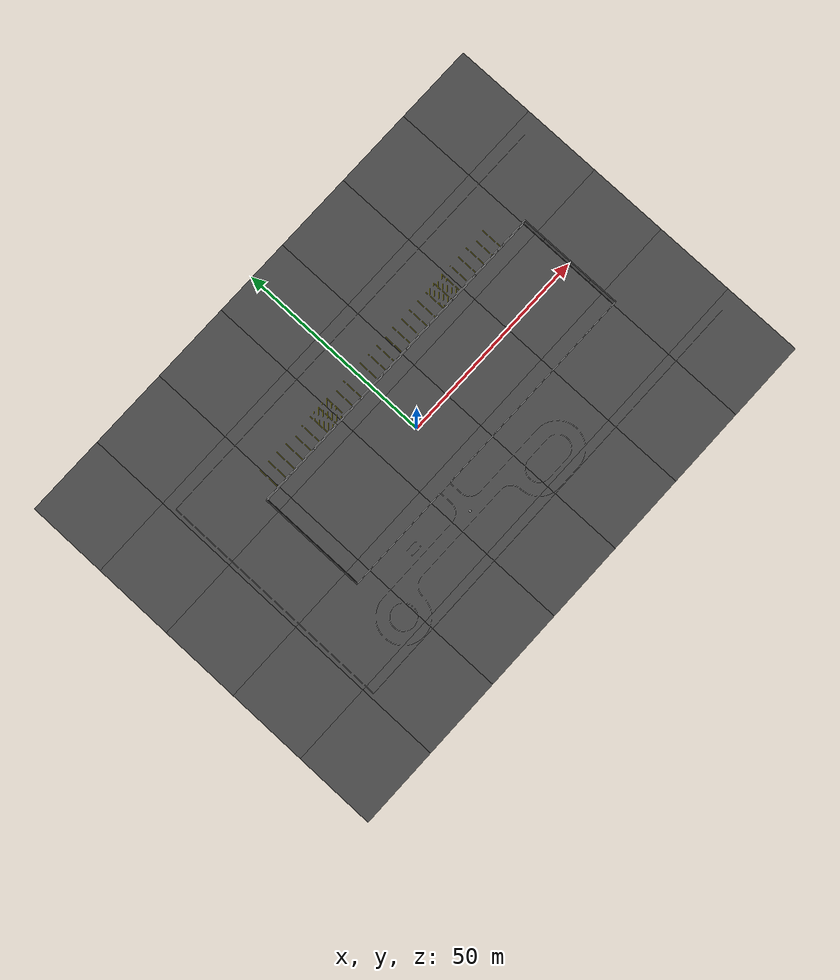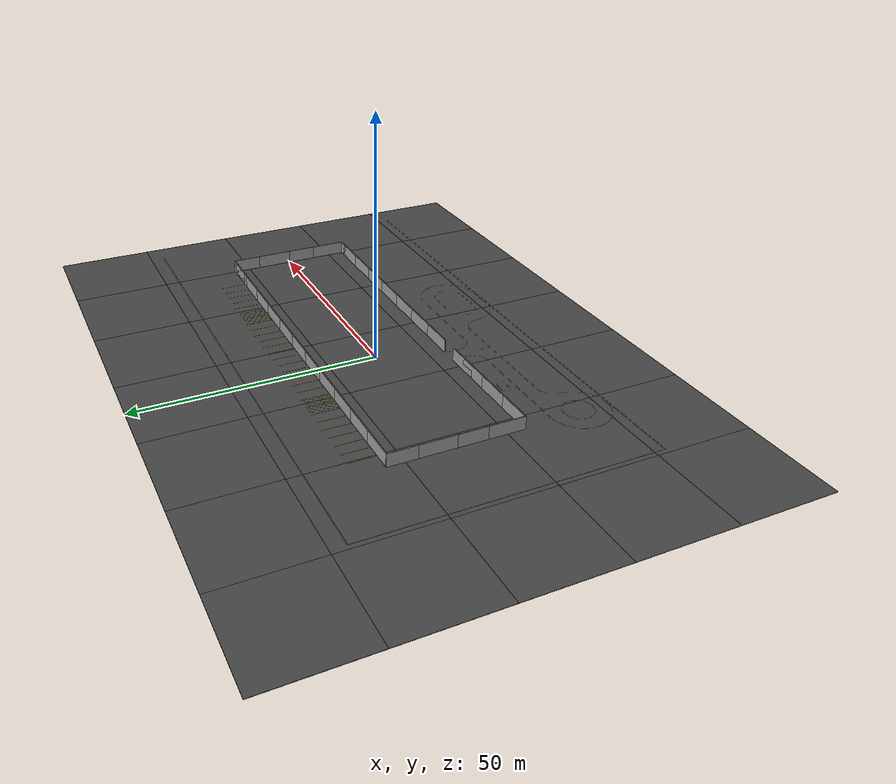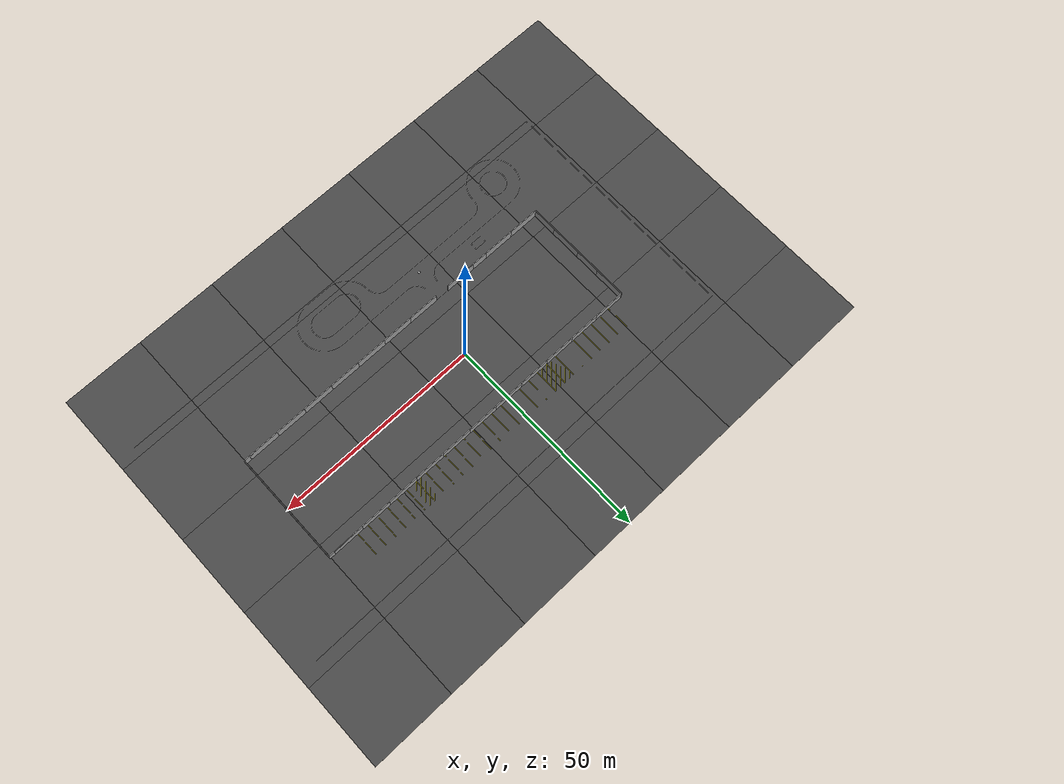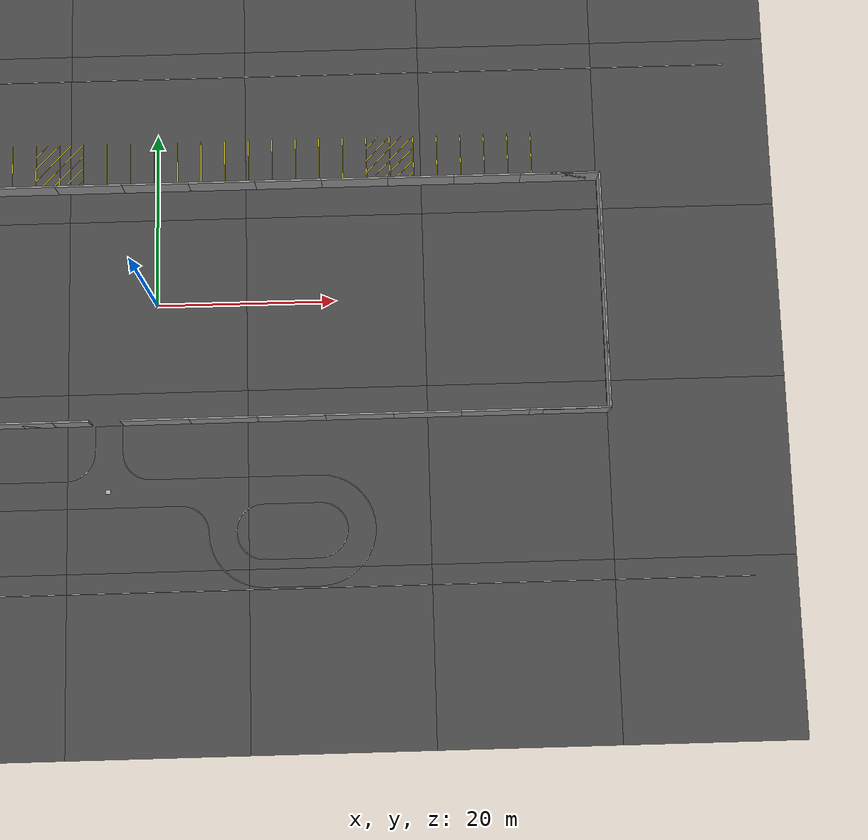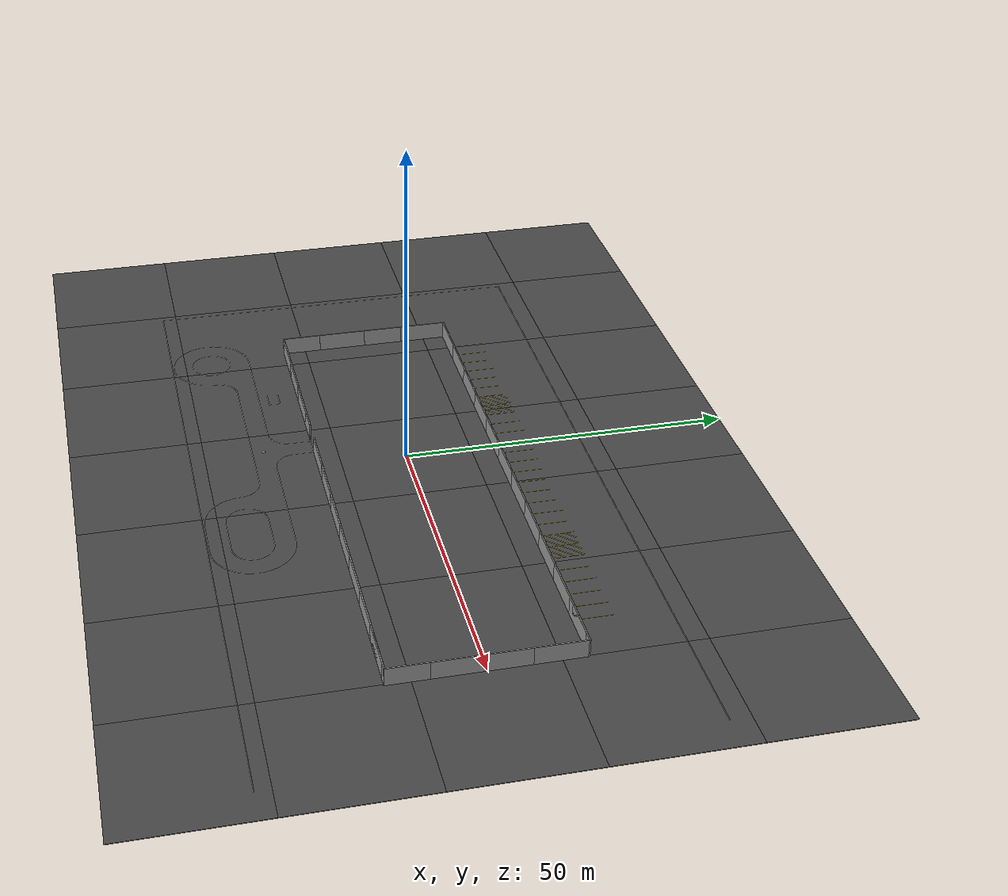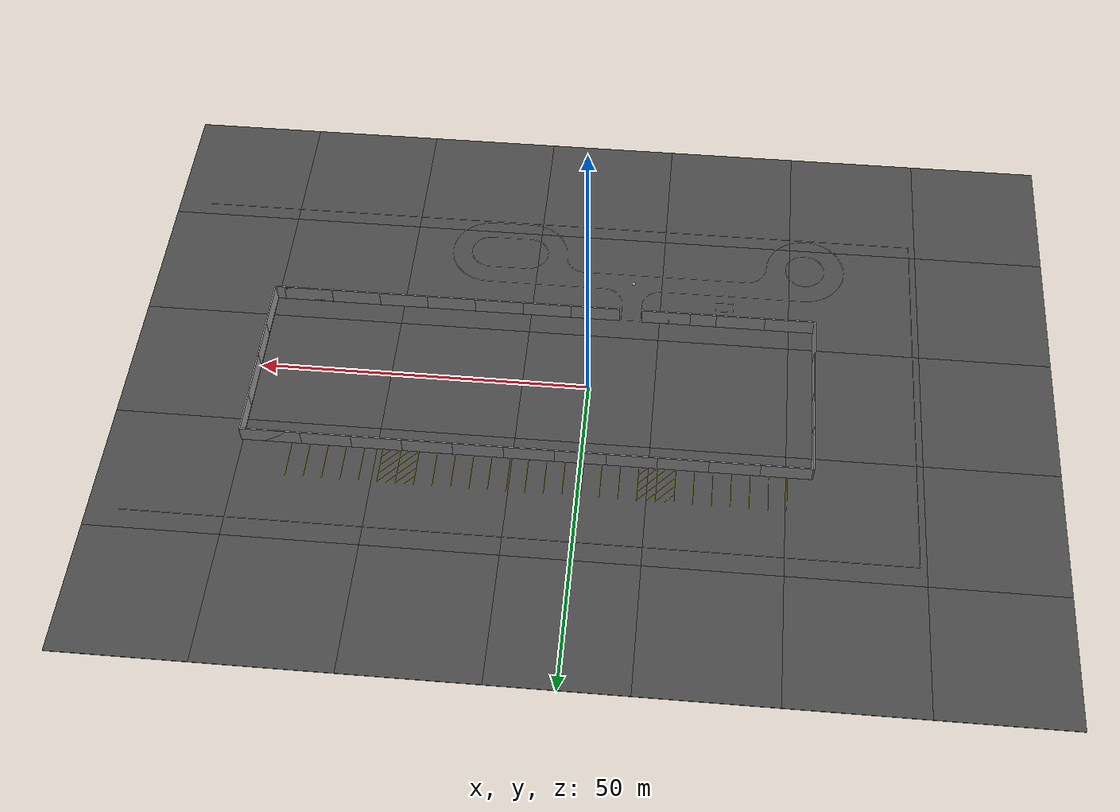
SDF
<sdf version="1.6">
 <world name="default">
  <light name="sun" type="directional">
   <pose>0 0 10 0 -0 0</pose>
   <diffuse>0.8 0.8 0.8 1</diffuse>
   <specular>0.2 0.2 0.2 1</specular>
   <attenuation>
    <range>1000</range>
    <constant>0.9</constant>
    <linear>0.01</linear>
    <quadratic>0.001</quadratic>
   </attenuation>
   <direction>-0.5 0.1 -0.9</direction>
   <spot><inner_angle>0</inner_angle><outer_angle>0</outer_angle><falloff>0</falloff></spot>
  </light>
  <gravity>0 0 -9.8</gravity>
  <magnetic_field>6e-06 2.3e-05 -4.2e-05</magnetic_field>
  <atmosphere type="adiabatic"/>
  <physics name="default_physics" default="0" type="ode">
   <max_step_size>0.001</max_step_size>
   <real_time_factor>1</real_time_factor>
   <real_time_update_rate>1000</real_time_update_rate>
  </physics>
  <scene><ambient>0.4 0.4 0.4 1</ambient><background>0.7 0.7 0.7 1</background><shadows>1</shadows></scene>
  <spherical_coordinates>
   <surface_model>EARTH_WGS84</surface_model>
   <latitude_deg>0</latitude_deg>
   <longitude_deg>0</longitude_deg>
   <elevation>0</elevation>
   <heading_deg>0</heading_deg>
  </spherical_coordinates>
  <audio><device>default</device></audio>
  <model name="grey_wall">
   <static>1</static>
   <link name="link">
    <pose>0 0 1.4 0 -0 0</pose>
    <collision name="collision"><geometry><box><size>7.5 0.2 2.8</size></box></geometry></collision>
    <visual name="visual">
     <cast_shadows>0</cast_shadows>
     <geometry><box><size>7.5 0.2 2.8</size></box></geometry>
     <material>
      <script>
       <uri>model://grey_wall/materials/scripts</uri>
       <uri>model://grey_wall/materials/textures</uri>
       <name>vrc/grey_wall</name>
      </script>
     </material>
    </visual>
   </link>
   <pose>0 -13.5 0 0 -0 0</pose>
  </model>
  <model name="grey_wall_0">
   <static>1</static>
   <link name="link">
    <pose>0 0 1.4 0 -0 0</pose>
    <collision name="collision"><geometry><box><size>7.5 0.2 2.8</size></box></geometry></collision>
    <visual name="visual">
     <cast_shadows>0</cast_shadows>
     <geometry><box><size>7.5 0.2 2.8</size></box></geometry>
     <material>
      <script>
       <uri>model://grey_wall/materials/scripts</uri>
       <uri>model://grey_wall/materials/textures</uri>
       <name>vrc/grey_wall</name>
      </script>
     </material>
    </visual>
   </link>
   <pose>7.5 -13.5 0 0 -0 0</pose>
  </model>
  <model name="grey_wall_1">
   <static>1</static>
   <link name="link">
    <pose>0 0 1.4 0 -0 0</pose>
    <collision name="collision"><geometry><box><size>7.5 0.2 2.8</size></box></geometry></collision>
    <visual name="visual">
     <cast_shadows>0</cast_shadows>
     <geometry><box><size>7.5 0.2 2.8</size></box></geometry>
     <material>
      <script>
       <uri>model://grey_wall/materials/scripts</uri>
       <uri>model://grey_wall/materials/textures</uri>
       <name>vrc/grey_wall</name>
      </script>
     </material>
    </visual>
   </link>
   <pose>-11 -13.5 0 0 -0 0</pose>
  </model>
  <model name="grey_wall_2">
   <static>1</static>
   <link name="link">
    <pose>0 0 1.4 0 -0 0</pose>
    <collision name="collision"><geometry><box><size>7.5 0.2 2.8</size></box></geometry></collision>
    <visual name="visual">
     <cast_shadows>0</cast_shadows>
     <geometry><box><size>7.5 0.2 2.8</size></box></geometry>
     <material>
      <script>
       <uri>model://grey_wall/materials/scripts</uri>
       <uri>model://grey_wall/materials/textures</uri>
       <name>vrc/grey_wall</name>
      </script>
     </material>
    </visual>
   </link>
   <pose>7.5 13.5 0 0 -0 0</pose>
  </model>
  <model name="grey_wall_3">
   <static>1</static>
   <link name="link">
    <pose>0 0 1.4 0 -0 0</pose>
    <collision name="collision"><geometry><box><size>7.5 0.2 2.8</size></box></geometry></collision>
    <visual name="visual">
     <cast_shadows>0</cast_shadows>
     <geometry><box><size>7.5 0.2 2.8</size></box></geometry>
     <material>
      <script>
       <uri>model://grey_wall/materials/scripts</uri>
       <uri>model://grey_wall/materials/textures</uri>
       <name>vrc/grey_wall</name>
      </script>
     </material>
    </visual>
   </link>
   <pose>0 13.5 0 0 -0 0</pose>
  </model>
  <model name="grey_wall_4">
   <static>1</static>
   <link name="link">
    <pose>0 0 1.4 0 -0 0</pose>
    <collision name="collision"><geometry><box><size>7.5 0.2 2.8</size></box></geometry></collision>
    <visual name="visual">
     <cast_shadows>0</cast_shadows>
     <geometry><box><size>7.5 0.2 2.8</size></box></geometry>
     <material>
      <script>
       <uri>model://grey_wall/materials/scripts</uri>
       <uri>model://grey_wall/materials/textures</uri>
       <name>vrc/grey_wall</name>
      </script>
     </material>
    </visual>
   </link>
   <pose>-7.5 13.5 0 0 -0 0</pose>
  </model>
  <model name="grey_wall_5">
   <static>1</static>
   <link name="link">
    <pose>0 0 1.4 0 -0 0</pose>
    <collision name="collision"><geometry><box><size>7.5 0.2 2.8</size></box></geometry></collision>
    <visual name="visual">
     <cast_shadows>0</cast_shadows>
     <geometry><box><size>7.5 0.2 2.8</size></box></geometry>
     <material>
      <script>
       <uri>model://grey_wall/materials/scripts</uri>
       <uri>model://grey_wall/materials/textures</uri>
       <name>vrc/grey_wall</name>
      </script>
     </material>
    </visual>
   </link>
   <pose>30 -13.5 0 0 -0 0</pose>
  </model>
  <model name="grey_wall_6">
   <static>1</static>
   <link name="link">
    <pose>0 0 1.4 0 -0 0</pose>
    <collision name="collision"><geometry><box><size>7.5 0.2 2.8</size></box></geometry></collision>
    <visual name="visual">
     <cast_shadows>0</cast_shadows>
     <geometry><box><size>7.5 0.2 2.8</size></box></geometry>
     <material>
      <script>
       <uri>model://grey_wall/materials/scripts</uri>
       <uri>model://grey_wall/materials/textures</uri>
       <name>vrc/grey_wall</name>
      </script>
     </material>
    </visual>
   </link>
   <pose>15 -13.5 0 0 -0 0</pose>
  </model>
  <model name="grey_wall_7">
   <static>1</static>
   <link name="link">
    <pose>0 0 1.4 0 -0 0</pose>
    <collision name="collision"><geometry><box><size>7.5 0.2 2.8</size></box></geometry></collision>
    <visual name="visual">
     <cast_shadows>0</cast_shadows>
     <geometry><box><size>7.5 0.2 2.8</size></box></geometry>
     <material>
      <script>
       <uri>model://grey_wall/materials/scripts</uri>
       <uri>model://grey_wall/materials/textures</uri>
       <name>vrc/grey_wall</name>
      </script>
     </material>
    </visual>
   </link>
   <pose>22.5 -13.5 0 0 -0 0</pose>
  </model>
  <model name="grey_wall_8">
   <static>1</static>
   <link name="link">
    <pose>0 0 1.4 0 -0 0</pose>
    <collision name="collision"><geometry><box><size>7.5 0.2 2.8</size></box></geometry></collision>
    <visual name="visual">
     <cast_shadows>0</cast_shadows>
     <geometry><box><size>7.5 0.2 2.8</size></box></geometry>
     <material>
      <script>
       <uri>model://grey_wall/materials/scripts</uri>
       <uri>model://grey_wall/materials/textures</uri>
       <name>vrc/grey_wall</name>
      </script>
     </material>
    </visual>
   </link>
   <pose>-15 -13.5 0 0 -0 0</pose>
  </model>
  <model name="grey_wall_9">
   <static>1</static>
   <link name="link">
    <pose>0 0 1.4 0 -0 0</pose>
    <collision name="collision"><geometry><box><size>7.5 0.2 2.8</size></box></geometry></collision>
    <visual name="visual">
     <cast_shadows>0</cast_shadows>
     <geometry><box><size>7.5 0.2 2.8</size></box></geometry>
     <material>
      <script>
       <uri>model://grey_wall/materials/scripts</uri>
       <uri>model://grey_wall/materials/textures</uri>
       <name>vrc/grey_wall</name>
      </script>
     </material>
    </visual>
   </link>
   <pose>-22.5 -13.5 0 0 -0 0</pose>
  </model>
  <model name="grey_wall_10">
   <static>1</static>
   <link name="link">
    <pose>0 0 1.4 0 -0 0</pose>
    <collision name="collision"><geometry><box><size>7.5 0.2 2.8</size></box></geometry></collision>
    <visual name="visual">
     <cast_shadows>0</cast_shadows>
     <geometry><box><size>7.5 0.2 2.8</size></box></geometry>
     <material>
      <script>
       <uri>model://grey_wall/materials/scripts</uri>
       <uri>model://grey_wall/materials/textures</uri>
       <name>vrc/grey_wall</name>
      </script>
     </material>
    </visual>
   </link>
   <pose>-30 -13.5 0 0 -0 0</pose>
  </model>
  <model name="grey_wall_11">
   <static>1</static>
   <link name="link">
    <pose>0 0 1.4 0 -0 0</pose>
    <collision name="collision"><geometry><box><size>7.5 0.2 2.8</size></box></geometry></collision>
    <visual name="visual">
     <cast_shadows>0</cast_shadows>
     <geometry><box><size>7.5 0.2 2.8</size></box></geometry>
     <material>
      <script>
       <uri>model://grey_wall/materials/scripts</uri>
       <uri>model://grey_wall/materials/textures</uri>
       <name>vrc/grey_wall</name>
      </script>
     </material>
    </visual>
   </link>
   <pose>15 13.5 0 0 -0 0</pose>
  </model>
  <model name="grey_wall_12">
   <static>1</static>
   <link name="link">
    <pose>0 0 1.4 0 -0 0</pose>
    <collision name="collision"><geometry><box><size>7.5 0.2 2.8</size></box></geometry></collision>
    <visual name="visual">
     <cast_shadows>0</cast_shadows>
     <geometry><box><size>7.5 0.2 2.8</size></box></geometry>
     <material>
      <script>
       <uri>model://grey_wall/materials/scripts</uri>
       <uri>model://grey_wall/materials/textures</uri>
       <name>vrc/grey_wall</name>
      </script>
     </material>
    </visual>
   </link>
   <pose>22.5 13.5 0 0 -0 0</pose>
  </model>
  <model name="grey_wall_13">
   <static>1</static>
   <link name="link">
    <pose>0 0 1.4 0 -0 0</pose>
    <collision name="collision"><geometry><box><size>7.5 0.2 2.8</size></box></geometry></collision>
    <visual name="visual">
     <cast_shadows>0</cast_shadows>
     <geometry><box><size>7.5 0.2 2.8</size></box></geometry>
     <material>
      <script>
       <uri>model://grey_wall/materials/scripts</uri>
       <uri>model://grey_wall/materials/textures</uri>
       <name>vrc/grey_wall</name>
      </script>
     </material>
    </visual>
   </link>
   <pose>30 13.5 0 0 -0 0</pose>
  </model>
  <model name="grey_wall_14">
   <static>1</static>
   <link name="link">
    <pose>0 0 1.4 0 -0 0</pose>
    <collision name="collision"><geometry><box><size>7.5 0.2 2.8</size></box></geometry></collision>
    <visual name="visual">
     <cast_shadows>0</cast_shadows>
     <geometry><box><size>7.5 0.2 2.8</size></box></geometry>
     <material>
      <script>
       <uri>model://grey_wall/materials/scripts</uri>
       <uri>model://grey_wall/materials/textures</uri>
       <name>vrc/grey_wall</name>
      </script>
     </material>
    </visual>
   </link>
   <pose>-15 13.5 0 0 -0 0</pose>
  </model>
  <model name="grey_wall_15">
   <static>1</static>
   <link name="link">
    <pose>0 0 1.4 0 -0 0</pose>
    <collision name="collision"><geometry><box><size>7.5 0.2 2.8</size></box></geometry></collision>
    <visual name="visual">
     <cast_shadows>0</cast_shadows>
     <geometry><box><size>7.5 0.2 2.8</size></box></geometry>
     <material>
      <script>
       <uri>model://grey_wall/materials/scripts</uri>
       <uri>model://grey_wall/materials/textures</uri>
       <name>vrc/grey_wall</name>
      </script>
     </material>
    </visual>
   </link>
   <pose>-22.5 13.5 0 0 -0 0</pose>
  </model>
  <model name="grey_wall_16">
   <static>1</static>
   <link name="link">
    <pose>0 0 1.4 0 -0 0</pose>
    <collision name="collision"><geometry><box><size>7.5 0.2 2.8</size></box></geometry></collision>
    <visual name="visual">
     <cast_shadows>0</cast_shadows>
     <geometry><box><size>7.5 0.2 2.8</size></box></geometry>
     <material>
      <script>
       <uri>model://grey_wall/materials/scripts</uri>
       <uri>model://grey_wall/materials/textures</uri>
       <name>vrc/grey_wall</name>
      </script>
     </material>
    </visual>
   </link>
   <pose>-30 13.5 0 0 -0 0</pose>
  </model>
  <model name="grey_wall_17">
   <static>1</static>
   <link name="link">
    <pose>0 0 1.4 0 -0 0</pose>
    <collision name="collision"><geometry><box><size>7.5 0.2 2.8</size></box></geometry></collision>
    <visual name="visual">
     <cast_shadows>0</cast_shadows>
     <geometry><box><size>7.5 0.2 2.8</size></box></geometry>
     <material>
      <script>
       <uri>model://grey_wall/materials/scripts</uri>
       <uri>model://grey_wall/materials/textures</uri>
       <name>vrc/grey_wall</name>
      </script>
     </material>
    </visual>
   </link>
   <pose>50.15 -9.85 0 0 -0 1.5708</pose>
  </model>
  <model name="grey_wall_18">
   <static>1</static>
   <link name="link">
    <pose>0 0 1.4 0 -0 0</pose>
    <collision name="collision"><geometry><box><size>7.5 0.2 2.8</size></box></geometry></collision>
    <visual name="visual">
     <cast_shadows>0</cast_shadows>
     <geometry><box><size>7.5 0.2 2.8</size></box></geometry>
     <material>
      <script>
       <uri>model://grey_wall/materials/scripts</uri>
       <uri>model://grey_wall/materials/textures</uri>
       <name>vrc/grey_wall</name>
      </script>
     </material>
    </visual>
   </link>
   <pose>50.15 9.85 0 0 -0 1.5708</pose>
  </model>
  <model name="grey_wall_19">
   <static>1</static>
   <link name="link">
    <pose>0 0 1.4 0 -0 0</pose>
    <collision name="collision"><geometry><box><size>7.5 0.2 2.8</size></box></geometry></collision>
    <visual name="visual">
     <cast_shadows>0</cast_shadows>
     <geometry><box><size>7.5 0.2 2.8</size></box></geometry>
     <material>
      <script>
       <uri>model://grey_wall/materials/scripts</uri>
       <uri>model://grey_wall/materials/textures</uri>
       <name>vrc/grey_wall</name>
      </script>
     </material>
    </visual>
   </link>
   <pose>50.15 -3.75 0 0 -0 1.5708</pose>
  </model>
  <model name="grey_wall_20">
   <static>1</static>
   <link name="link">
    <pose>0 0 1.4 0 -0 0</pose>
    <collision name="collision"><geometry><box><size>7.5 0.2 2.8</size></box></geometry></collision>
    <visual name="visual">
     <cast_shadows>0</cast_shadows>
     <geometry><box><size>7.5 0.2 2.8</size></box></geometry>
     <material>
      <script>
       <uri>model://grey_wall/materials/scripts</uri>
       <uri>model://grey_wall/materials/textures</uri>
       <name>vrc/grey_wall</name>
      </script>
     </material>
    </visual>
   </link>
   <pose>50.15 3.75 0 0 -0 1.5708</pose>
  </model>
  <model name="grey_wall_21">
   <static>1</static>
   <link name="link">
    <pose>0 0 1.4 0 -0 0</pose>
    <collision name="collision"><geometry><box><size>7.5 0.2 2.8</size></box></geometry></collision>
    <visual name="visual">
     <cast_shadows>0</cast_shadows>
     <geometry><box><size>7.5 0.2 2.8</size></box></geometry>
     <material>
      <script>
       <uri>model://grey_wall/materials/scripts</uri>
       <uri>model://grey_wall/materials/textures</uri>
       <name>vrc/grey_wall</name>
      </script>
     </material>
    </visual>
   </link>
   <pose>-33.85 3.75 0 0 -0 1.5708</pose>
  </model>
  <model name="grey_wall_22">
   <static>1</static>
   <link name="link">
    <pose>0 0 1.4 0 -0 0</pose>
    <collision name="collision"><geometry><box><size>7.5 0.2 2.8</size></box></geometry></collision>
    <visual name="visual">
     <cast_shadows>0</cast_shadows>
     <geometry><box><size>7.5 0.2 2.8</size></box></geometry>
     <material>
      <script>
       <uri>model://grey_wall/materials/scripts</uri>
       <uri>model://grey_wall/materials/textures</uri>
       <name>vrc/grey_wall</name>
      </script>
     </material>
    </visual>
   </link>
   <pose>-33.85 9.85 0 0 -0 1.5708</pose>
  </model>
  <model name="grey_wall_23">
   <static>1</static>
   <link name="link">
    <pose>0 0 1.4 0 -0 0</pose>
    <collision name="collision"><geometry><box><size>7.5 0.2 2.8</size></box></geometry></collision>
    <visual name="visual">
     <cast_shadows>0</cast_shadows>
     <geometry><box><size>7.5 0.2 2.8</size></box></geometry>
     <material>
      <script>
       <uri>model://grey_wall/materials/scripts</uri>
       <uri>model://grey_wall/materials/textures</uri>
       <name>vrc/grey_wall</name>
      </script>
     </material>
    </visual>
   </link>
   <pose>-33.85 -3.75 0 0 -0 1.5708</pose>
  </model>
  <model name="grey_wall_24">
   <static>1</static>
   <link name="link">
    <pose>0 0 1.4 0 -0 0</pose>
    <collision name="collision"><geometry><box><size>7.5 0.2 2.8</size></box></geometry></collision>
    <visual name="visual">
     <cast_shadows>0</cast_shadows>
     <geometry><box><size>7.5 0.2 2.8</size></box></geometry>
     <material>
      <script>
       <uri>model://grey_wall/materials/scripts</uri>
       <uri>model://grey_wall/materials/textures</uri>
       <name>vrc/grey_wall</name>
      </script>
     </material>
    </visual>
   </link>
   <pose>-33.85 -9.85 0 0 -0 1.5708</pose>
  </model>
  <model name="asphalt_plane">
   <static>1</static>
   <link name="link">
    <collision name="collision"><geometry><box><size>20 20 0.1</size></box></geometry></collision>
    <visual name="visual">
     <cast_shadows>0</cast_shadows>
     <geometry><box><size>20 20 0.1</size></box></geometry>
     <material>
      <script>
       <uri>model://asphalt_plane/materials/scripts</uri>
       <uri>model://asphalt_plane/materials/textures</uri>
       <name>vrc/asphalt</name>
      </script>
     </material>
    </visual>
   </link>
  </model>
  <model name="asphalt_plane_0">
   <static>1</static>
   <link name="link">
    <collision name="collision"><geometry><box><size>20 20 0.1</size></box></geometry></collision>
    <visual name="visual">
     <cast_shadows>0</cast_shadows>
     <geometry><box><size>20 20 0.1</size></box></geometry>
     <material>
      <script>
       <uri>model://asphalt_plane/materials/scripts</uri>
       <uri>model://asphalt_plane/materials/textures</uri>
       <name>vrc/asphalt</name>
      </script>
     </material>
    </visual>
   </link>
   <pose>-20 0 0 0 -0 0</pose>
  </model>
  <model name="asphalt_plane_1">
   <static>1</static>
   <link name="link">
    <collision name="collision"><geometry><box><size>20 20 0.1</size></box></geometry></collision>
    <visual name="visual">
     <cast_shadows>0</cast_shadows>
     <geometry><box><size>20 20 0.1</size></box></geometry>
     <material>
      <script>
       <uri>model://asphalt_plane/materials/scripts</uri>
       <uri>model://asphalt_plane/materials/textures</uri>
       <name>vrc/asphalt</name>
      </script>
     </material>
    </visual>
   </link>
   <pose>-40 0 0 0 -0 0</pose>
  </model>
  <model name="asphalt_plane_2">
   <static>1</static>
   <link name="link">
    <collision name="collision"><geometry><box><size>20 20 0.1</size></box></geometry></collision>
    <visual name="visual">
     <cast_shadows>0</cast_shadows>
     <geometry><box><size>20 20 0.1</size></box></geometry>
     <material>
      <script>
       <uri>model://asphalt_plane/materials/scripts</uri>
       <uri>model://asphalt_plane/materials/textures</uri>
       <name>vrc/asphalt</name>
      </script>
     </material>
    </visual>
   </link>
   <pose>20 0 0 0 -0 0</pose>
  </model>
  <model name="asphalt_plane_3">
   <static>1</static>
   <link name="link">
    <collision name="collision"><geometry><box><size>20 20 0.1</size></box></geometry></collision>
    <visual name="visual">
     <cast_shadows>0</cast_shadows>
     <geometry><box><size>20 20 0.1</size></box></geometry>
     <material>
      <script>
       <uri>model://asphalt_plane/materials/scripts</uri>
       <uri>model://asphalt_plane/materials/textures</uri>
       <name>vrc/asphalt</name>
      </script>
     </material>
    </visual>
   </link>
   <pose>40 0 0 0 -0 0</pose>
  </model>
  <model name="asphalt_plane_4">
   <static>1</static>
   <link name="link">
    <collision name="collision"><geometry><box><size>20 20 0.1</size></box></geometry></collision>
    <visual name="visual">
     <cast_shadows>0</cast_shadows>
     <geometry><box><size>20 20 0.1</size></box></geometry>
     <material>
      <script>
       <uri>model://asphalt_plane/materials/scripts</uri>
       <uri>model://asphalt_plane/materials/textures</uri>
       <name>vrc/asphalt</name>
      </script>
     </material>
    </visual>
   </link>
   <pose>0 -20 0 0 -0 0</pose>
  </model>
  <model name="asphalt_plane_5">
   <static>1</static>
   <link name="link">
    <collision name="collision"><geometry><box><size>20 20 0.1</size></box></geometry></collision>
    <visual name="visual">
     <cast_shadows>0</cast_shadows>
     <geometry><box><size>20 20 0.1</size></box></geometry>
     <material>
      <script>
       <uri>model://asphalt_plane/materials/scripts</uri>
       <uri>model://asphalt_plane/materials/textures</uri>
       <name>vrc/asphalt</name>
      </script>
     </material>
    </visual>
   </link>
   <pose>-20 -20 0 0 -0 0</pose>
  </model>
  <model name="asphalt_plane_6">
   <static>1</static>
   <link name="link">
    <collision name="collision"><geometry><box><size>20 20 0.1</size></box></geometry></collision>
    <visual name="visual">
     <cast_shadows>0</cast_shadows>
     <geometry><box><size>20 20 0.1</size></box></geometry>
     <material>
      <script>
       <uri>model://asphalt_plane/materials/scripts</uri>
       <uri>model://asphalt_plane/materials/textures</uri>
       <name>vrc/asphalt</name>
      </script>
     </material>
    </visual>
   </link>
   <pose>-40 -20 0 0 -0 0</pose>
  </model>
  <model name="asphalt_plane_7">
   <static>1</static>
   <link name="link">
    <collision name="collision"><geometry><box><size>20 20 0.1</size></box></geometry></collision>
    <visual name="visual">
     <cast_shadows>0</cast_shadows>
     <geometry><box><size>20 20 0.1</size></box></geometry>
     <material>
      <script>
       <uri>model://asphalt_plane/materials/scripts</uri>
       <uri>model://asphalt_plane/materials/textures</uri>
       <name>vrc/asphalt</name>
      </script>
     </material>
    </visual>
   </link>
   <pose>20 -20 0 0 -0 0</pose>
  </model>
  <model name="asphalt_plane_8">
   <static>1</static>
   <link name="link">
    <collision name="collision"><geometry><box><size>20 20 0.1</size></box></geometry></collision>
    <visual name="visual">
     <cast_shadows>0</cast_shadows>
     <geometry><box><size>20 20 0.1</size></box></geometry>
     <material>
      <script>
       <uri>model://asphalt_plane/materials/scripts</uri>
       <uri>model://asphalt_plane/materials/textures</uri>
       <name>vrc/asphalt</name>
      </script>
     </material>
    </visual>
   </link>
   <pose>40 -20 0 0 -0 0</pose>
  </model>
  <model name="asphalt_plane_9">
   <static>1</static>
   <link name="link">
    <collision name="collision"><geometry><box><size>20 20 0.1</size></box></geometry></collision>
    <visual name="visual">
     <cast_shadows>0</cast_shadows>
     <geometry><box><size>20 20 0.1</size></box></geometry>
     <material>
      <script>
       <uri>model://asphalt_plane/materials/scripts</uri>
       <uri>model://asphalt_plane/materials/textures</uri>
       <name>vrc/asphalt</name>
      </script>
     </material>
    </visual>
   </link>
   <pose>-40 20 0 0 -0 0</pose>
  </model>
  <model name="asphalt_plane_10">
   <static>1</static>
   <link name="link">
    <collision name="collision"><geometry><box><size>20 20 0.1</size></box></geometry></collision>
    <visual name="visual">
     <cast_shadows>0</cast_shadows>
     <geometry><box><size>20 20 0.1</size></box></geometry>
     <material>
      <script>
       <uri>model://asphalt_plane/materials/scripts</uri>
       <uri>model://asphalt_plane/materials/textures</uri>
       <name>vrc/asphalt</name>
      </script>
     </material>
    </visual>
   </link>
   <pose>-20 20 0 0 -0 0</pose>
  </model>
  <model name="asphalt_plane_11">
   <static>1</static>
   <link name="link">
    <collision name="collision"><geometry><box><size>20 20 0.1</size></box></geometry></collision>
    <visual name="visual">
     <cast_shadows>0</cast_shadows>
     <geometry><box><size>20 20 0.1</size></box></geometry>
     <material>
      <script>
       <uri>model://asphalt_plane/materials/scripts</uri>
       <uri>model://asphalt_plane/materials/textures</uri>
       <name>vrc/asphalt</name>
      </script>
     </material>
    </visual>
   </link>
   <pose>0 20 0 0 -0 0</pose>
  </model>
  <model name="asphalt_plane_12">
   <static>1</static>
   <link name="link">
    <collision name="collision"><geometry><box><size>20 20 0.1</size></box></geometry></collision>
    <visual name="visual">
     <cast_shadows>0</cast_shadows>
     <geometry><box><size>20 20 0.1</size></box></geometry>
     <material>
      <script>
       <uri>model://asphalt_plane/materials/scripts</uri>
       <uri>model://asphalt_plane/materials/textures</uri>
       <name>vrc/asphalt</name>
      </script>
     </material>
    </visual>
   </link>
   <pose>20 20 0 0 -0 0</pose>
  </model>
  <model name="asphalt_plane_13">
   <static>1</static>
   <link name="link">
    <collision name="collision"><geometry><box><size>20 20 0.1</size></box></geometry></collision>
    <visual name="visual">
     <cast_shadows>0</cast_shadows>
     <geometry><box><size>20 20 0.1</size></box></geometry>
     <material>
      <script>
       <uri>model://asphalt_plane/materials/scripts</uri>
       <uri>model://asphalt_plane/materials/textures</uri>
       <name>vrc/asphalt</name>
      </script>
     </material>
    </visual>
   </link>
   <pose>40 20 0 0 -0 0</pose>
  </model>
  <model name="yellow_point">
   <static>1</static>
   <link name="link">
    <collision name="collision">
     <geometry><plane><normal>0 0 1</normal><size>0.5 0.5</size></plane></geometry>
     <surface><friction><ode><mu>100</mu><mu2>50</mu2></ode></friction></surface>
    </collision>
    <visual name="visual">
     <cast_shadows>0</cast_shadows>
     <geometry><plane><normal>0 0 1</normal><size>0.5 0.5</size></plane></geometry>
     <material>
      <script>
       <uri>model://yellow_point/materials/scripts</uri>
       <uri>model://yellow_point/materials/textures/</uri>
       <name>MyGroundPlane/Image</name>
      </script>
     </material>
    </visual>
   </link>
   <pose>-5.5 -21 0.06 0 -0 0</pose>
  </model>
  <model name="asphalt_plane_14">
   <static>1</static>
   <link name="link">
    <collision name="collision"><geometry><box><size>20 20 0.1</size></box></geometry></collision>
    <visual name="visual">
     <cast_shadows>0</cast_shadows>
     <geometry><box><size>20 20 0.1</size></box></geometry>
     <material>
      <script>
       <uri>model://asphalt_plane/materials/scripts</uri>
       <uri>model://asphalt_plane/materials/textures</uri>
       <name>vrc/asphalt</name>
      </script>
     </material>
    </visual>
   </link>
   <pose>60 0 0 0 -0 0</pose>
  </model>
  <model name="asphalt_plane_15">
   <static>1</static>
   <link name="link">
    <collision name="collision"><geometry><box><size>20 20 0.1</size></box></geometry></collision>
    <visual name="visual">
     <cast_shadows>0</cast_shadows>
     <geometry><box><size>20 20 0.1</size></box></geometry>
     <material>
      <script>
       <uri>model://asphalt_plane/materials/scripts</uri>
       <uri>model://asphalt_plane/materials/textures</uri>
       <name>vrc/asphalt</name>
      </script>
     </material>
    </visual>
   </link>
   <pose>60 20 0 0 -0 0</pose>
  </model>
  <model name="asphalt_plane_16">
   <static>1</static>
   <link name="link">
    <collision name="collision"><geometry><box><size>20 20 0.1</size></box></geometry></collision>
    <visual name="visual">
     <cast_shadows>0</cast_shadows>
     <geometry><box><size>20 20 0.1</size></box></geometry>
     <material>
      <script>
       <uri>model://asphalt_plane/materials/scripts</uri>
       <uri>model://asphalt_plane/materials/textures</uri>
       <name>vrc/asphalt</name>
      </script>
     </material>
    </visual>
   </link>
   <pose>60 -20 0 0 -0 0</pose>
  </model>
  <model name="asphalt_plane_17">
   <static>1</static>
   <link name="link">
    <collision name="collision"><geometry><box><size>20 20 0.1</size></box></geometry></collision>
    <visual name="visual">
     <cast_shadows>0</cast_shadows>
     <geometry><box><size>20 20 0.1</size></box></geometry>
     <material>
      <script>
       <uri>model://asphalt_plane/materials/scripts</uri>
       <uri>model://asphalt_plane/materials/textures</uri>
       <name>vrc/asphalt</name>
      </script>
     </material>
    </visual>
   </link>
   <pose>40 -40 0 0 -0 0</pose>
  </model>
  <model name="asphalt_plane_18">
   <static>1</static>
   <link name="link">
    <collision name="collision"><geometry><box><size>20 20 0.1</size></box></geometry></collision>
    <visual name="visual">
     <cast_shadows>0</cast_shadows>
     <geometry><box><size>20 20 0.1</size></box></geometry>
     <material>
      <script>
       <uri>model://asphalt_plane/materials/scripts</uri>
       <uri>model://asphalt_plane/materials/textures</uri>
       <name>vrc/asphalt</name>
      </script>
     </material>
    </visual>
   </link>
   <pose>60 -40 0 0 -0 0</pose>
  </model>
  <model name="asphalt_plane_19">
   <static>1</static>
   <link name="link">
    <collision name="collision"><geometry><box><size>20 20 0.1</size></box></geometry></collision>
    <visual name="visual">
     <cast_shadows>0</cast_shadows>
     <geometry><box><size>20 20 0.1</size></box></geometry>
     <material>
      <script>
       <uri>model://asphalt_plane/materials/scripts</uri>
       <uri>model://asphalt_plane/materials/textures</uri>
       <name>vrc/asphalt</name>
      </script>
     </material>
    </visual>
   </link>
   <pose>20 -40 0 0 -0 0</pose>
  </model>
  <model name="asphalt_plane_20">
   <static>1</static>
   <link name="link">
    <collision name="collision"><geometry><box><size>20 20 0.1</size></box></geometry></collision>
    <visual name="visual">
     <cast_shadows>0</cast_shadows>
     <geometry><box><size>20 20 0.1</size></box></geometry>
     <material>
      <script>
       <uri>model://asphalt_plane/materials/scripts</uri>
       <uri>model://asphalt_plane/materials/textures</uri>
       <name>vrc/asphalt</name>
      </script>
     </material>
    </visual>
   </link>
   <pose>0 -40 0 0 -0 0</pose>
  </model>
  <model name="asphalt_plane_21">
   <static>1</static>
   <link name="link">
    <collision name="collision"><geometry><box><size>20 20 0.1</size></box></geometry></collision>
    <visual name="visual">
     <cast_shadows>0</cast_shadows>
     <geometry><box><size>20 20 0.1</size></box></geometry>
     <material>
      <script>
       <uri>model://asphalt_plane/materials/scripts</uri>
       <uri>model://asphalt_plane/materials/textures</uri>
       <name>vrc/asphalt</name>
      </script>
     </material>
    </visual>
   </link>
   <pose>-20 -40 0 0 -0 0</pose>
  </model>
  <model name="asphalt_plane_22">
   <static>1</static>
   <link name="link">
    <collision name="collision"><geometry><box><size>20 20 0.1</size></box></geometry></collision>
    <visual name="visual">
     <cast_shadows>0</cast_shadows>
     <geometry><box><size>20 20 0.1</size></box></geometry>
     <material>
      <script>
       <uri>model://asphalt_plane/materials/scripts</uri>
       <uri>model://asphalt_plane/materials/textures</uri>
       <name>vrc/asphalt</name>
      </script>
     </material>
    </visual>
   </link>
   <pose>-40 -40 0 0 -0 0</pose>
  </model>
  <model name="asphalt_plane_23">
   <static>1</static>
   <link name="link">
    <collision name="collision"><geometry><box><size>20 20 0.1</size></box></geometry></collision>
    <visual name="visual">
     <cast_shadows>0</cast_shadows>
     <geometry><box><size>20 20 0.1</size></box></geometry>
     <material>
      <script>
       <uri>model://asphalt_plane/materials/scripts</uri>
       <uri>model://asphalt_plane/materials/textures</uri>
       <name>vrc/asphalt</name>
      </script>
     </material>
    </visual>
   </link>
   <pose>-60 -40 0 0 -0 0</pose>
  </model>
  <model name="asphalt_plane_24">
   <static>1</static>
   <link name="link">
    <collision name="collision"><geometry><box><size>20 20 0.1</size></box></geometry></collision>
    <visual name="visual">
     <cast_shadows>0</cast_shadows>
     <geometry><box><size>20 20 0.1</size></box></geometry>
     <material>
      <script>
       <uri>model://asphalt_plane/materials/scripts</uri>
       <uri>model://asphalt_plane/materials/textures</uri>
       <name>vrc/asphalt</name>
      </script>
     </material>
    </visual>
   </link>
   <pose>-60 -20 0 0 -0 0</pose>
  </model>
  <model name="asphalt_plane_25">
   <static>1</static>
   <link name="link">
    <collision name="collision"><geometry><box><size>20 20 0.1</size></box></geometry></collision>
    <visual name="visual">
     <cast_shadows>0</cast_shadows>
     <geometry><box><size>20 20 0.1</size></box></geometry>
     <material>
      <script>
       <uri>model://asphalt_plane/materials/scripts</uri>
       <uri>model://asphalt_plane/materials/textures</uri>
       <name>vrc/asphalt</name>
      </script>
     </material>
    </visual>
   </link>
   <pose>-60 0 0 0 -0 0</pose>
  </model>
  <model name="asphalt_plane_26">
   <static>1</static>
   <link name="link">
    <collision name="collision"><geometry><box><size>20 20 0.1</size></box></geometry></collision>
    <visual name="visual">
     <cast_shadows>0</cast_shadows>
     <geometry><box><size>20 20 0.1</size></box></geometry>
     <material>
      <script>
       <uri>model://asphalt_plane/materials/scripts</uri>
       <uri>model://asphalt_plane/materials/textures</uri>
       <name>vrc/asphalt</name>
      </script>
     </material>
    </visual>
   </link>
   <pose>-60 20 0 0 -0 0</pose>
  </model>
  <model name="asphalt_plane_27">
   <static>1</static>
   <link name="link">
    <collision name="collision"><geometry><box><size>20 20 0.1</size></box></geometry></collision>
    <visual name="visual">
     <cast_shadows>0</cast_shadows>
     <geometry><box><size>20 20 0.1</size></box></geometry>
     <material>
      <script>
       <uri>model://asphalt_plane/materials/scripts</uri>
       <uri>model://asphalt_plane/materials/textures</uri>
       <name>vrc/asphalt</name>
      </script>
     </material>
    </visual>
   </link>
   <pose>-60 40 0 0 -0 0</pose>
  </model>
  <model name="asphalt_plane_28">
   <static>1</static>
   <link name="link">
    <collision name="collision"><geometry><box><size>20 20 0.1</size></box></geometry></collision>
    <visual name="visual">
     <cast_shadows>0</cast_shadows>
     <geometry><box><size>20 20 0.1</size></box></geometry>
     <material>
      <script>
       <uri>model://asphalt_plane/materials/scripts</uri>
       <uri>model://asphalt_plane/materials/textures</uri>
       <name>vrc/asphalt</name>
      </script>
     </material>
    </visual>
   </link>
   <pose>-40 40 0 0 -0 0</pose>
  </model>
  <model name="asphalt_plane_29">
   <static>1</static>
   <link name="link">
    <collision name="collision"><geometry><box><size>20 20 0.1</size></box></geometry></collision>
    <visual name="visual">
     <cast_shadows>0</cast_shadows>
     <geometry><box><size>20 20 0.1</size></box></geometry>
     <material>
      <script>
       <uri>model://asphalt_plane/materials/scripts</uri>
       <uri>model://asphalt_plane/materials/textures</uri>
       <name>vrc/asphalt</name>
      </script>
     </material>
    </visual>
   </link>
   <pose>-20 40 0 0 -0 0</pose>
  </model>
  <model name="asphalt_plane_30">
   <static>1</static>
   <link name="link">
    <collision name="collision"><geometry><box><size>20 20 0.1</size></box></geometry></collision>
    <visual name="visual">
     <cast_shadows>0</cast_shadows>
     <geometry><box><size>20 20 0.1</size></box></geometry>
     <material>
      <script>
       <uri>model://asphalt_plane/materials/scripts</uri>
       <uri>model://asphalt_plane/materials/textures</uri>
       <name>vrc/asphalt</name>
      </script>
     </material>
    </visual>
   </link>
   <pose>0 40 0 0 -0 0</pose>
  </model>
  <model name="asphalt_plane_31">
   <static>1</static>
   <link name="link">
    <collision name="collision"><geometry><box><size>20 20 0.1</size></box></geometry></collision>
    <visual name="visual">
     <cast_shadows>0</cast_shadows>
     <geometry><box><size>20 20 0.1</size></box></geometry>
     <material>
      <script>
       <uri>model://asphalt_plane/materials/scripts</uri>
       <uri>model://asphalt_plane/materials/textures</uri>
       <name>vrc/asphalt</name>
      </script>
     </material>
    </visual>
   </link>
   <pose>20 40 0 0 -0 0</pose>
  </model>
  <model name="asphalt_plane_32">
   <static>1</static>
   <link name="link">
    <collision name="collision"><geometry><box><size>20 20 0.1</size></box></geometry></collision>
    <visual name="visual">
     <cast_shadows>0</cast_shadows>
     <geometry><box><size>20 20 0.1</size></box></geometry>
     <material>
      <script>
       <uri>model://asphalt_plane/materials/scripts</uri>
       <uri>model://asphalt_plane/materials/textures</uri>
       <name>vrc/asphalt</name>
      </script>
     </material>
    </visual>
   </link>
   <pose>40 40 0 0 -0 0</pose>
  </model>
  <model name="asphalt_plane_33">
   <static>1</static>
   <link name="link">
    <collision name="collision"><geometry><box><size>20 20 0.1</size></box></geometry></collision>
    <visual name="visual">
     <cast_shadows>0</cast_shadows>
     <geometry><box><size>20 20 0.1</size></box></geometry>
     <material>
      <script>
       <uri>model://asphalt_plane/materials/scripts</uri>
       <uri>model://asphalt_plane/materials/textures</uri>
       <name>vrc/asphalt</name>
      </script>
     </material>
    </visual>
   </link>
   <pose>60 40 0 0 -0 0</pose>
  </model>
  <model name="track_curb">
   <static>1</static>
   <link name="link">
    <inertial>
     <pose>0 0 1 0 -0 0</pose>
     <mass>5</mass>
     <inertia><ixx>0.833</ixx><iyy>0.833</iyy><izz>0.833</izz><ixy>0</ixy><ixz>0</ixz><iyz>0</iyz></inertia>
    </inertial>
    <collision name="collision">
     <pose>0 0 1 0 -0 0</pose>
     <geometry>
      <mesh><uri>model://track_curb/meshes/track.dae</uri><scale>0.3048 0.3048 0.3048</scale></mesh>
     </geometry>
    </collision>
    <visual name="visual">
     <pose>0 0 1 0 -0 0</pose>
     <geometry>
      <mesh><uri>model://track_curb/meshes/track.dae</uri><scale>0.3048 0.3048 0.3048</scale></mesh>
     </geometry>
     <material>
      <script>
       <uri>model://track_curb/materials/scripts</uri>
       <uri>model://track_curb/materials/textures/</uri>
       <name>white</name>
      </script>
     </material>
    </visual>
   </link>
   <pose>24 -32 -1.256 0 -0 3.14159</pose>
  </model>
  <model name="54m_redline">
   <static>1</static>
   <link name="link">
    <collision name="collision">
     <geometry><plane><normal>0 0 1</normal><size>59.3 0.1</size></plane></geometry>
     <surface><friction><ode><mu>100</mu><mu2>50</mu2></ode></friction></surface>
    </collision>
    <visual name="visual">
     <cast_shadows>0</cast_shadows>
     <geometry><plane><normal>0 0 1</normal><size>59.3 0.1</size></plane></geometry>
     <material>
      <script>
       <uri>model://54m_redline/materials/scripts</uri>
       <uri>model://54m_redline/materials/textures/</uri>
       <name>MyGroundPlane/Image</name>
      </script>
     </material>
    </visual>
   </link>
   <pose>65.3 -2.6 0.06 0 -0 1.5707</pose>
  </model>
  <model name="54m_redline_0">
   <static>1</static>
   <link name="link">
    <collision name="collision">
     <geometry><plane><normal>0 0 1</normal><size>59.3 0.1</size></plane></geometry>
     <surface><friction><ode><mu>100</mu><mu2>50</mu2></ode></friction></surface>
    </collision>
    <visual name="visual">
     <cast_shadows>0</cast_shadows>
     <geometry><plane><normal>0 0 1</normal><size>59.3 0.1</size></plane></geometry>
     <material>
      <script>
       <uri>model://54m_redline/materials/scripts</uri>
       <uri>model://54m_redline/materials/textures/</uri>
       <name>MyGroundPlane/Image</name>
      </script>
     </material>
    </visual>
   </link>
   <pose>-49 -2.6 0.06 0 -0 1.5707</pose>
  </model>
  <model name="parking_line">
   <static>1</static>
   <link name="link">
    <inertial>
     <pose>0 0 1 0 -0 0</pose>
     <mass>5</mass>
     <inertia><ixx>0.833</ixx><iyy>0.833</iyy><izz>0.833</izz><ixy>0</ixy><ixz>0</ixz><iyz>0</iyz></inertia>
    </inertial>
    <collision name="collision">
     <pose>0 0 1 0 -0 0</pose>
     <geometry><mesh><uri>model://parking_line/meshes/parking_line.dae</uri><scale>1 1 1</scale></mesh></geometry>
    </collision>
    <visual name="visual">
     <pose>0 0 1 0 -0 0</pose>
     <geometry><mesh><uri>model://parking_line/meshes/parking_line.dae</uri><scale>1 1 1</scale></mesh></geometry>
     <material>
      <script>
       <uri>model://parking_line/materials/scripts</uri>
       <uri>model://parking_line/materials/textures/</uri>
       <name>yellow</name>
      </script>
     </material>
    </visual>
   </link>
   <pose>-30.15 13.6 -1.049 0 -0 1.5707</pose>
  </model>
  <model name="parking_line_0">
   <static>1</static>
   <link name="link">
    <inertial>
     <pose>0 0 1 0 -0 0</pose>
     <mass>5</mass>
     <inertia><ixx>0.833</ixx><iyy>0.833</iyy><izz>0.833</izz><ixy>0</ixy><ixz>0</ixz><iyz>0</iyz></inertia>
    </inertial>
    <collision name="collision">
     <pose>0 0 1 0 -0 0</pose>
     <geometry><mesh><uri>model://parking_line/meshes/parking_line.dae</uri><scale>1 1 1</scale></mesh></geometry>
    </collision>
    <visual name="visual">
     <pose>0 0 1 0 -0 0</pose>
     <geometry><mesh><uri>model://parking_line/meshes/parking_line.dae</uri><scale>1 1 1</scale></mesh></geometry>
     <material>
      <script>
       <uri>model://parking_line/materials/scripts</uri>
       <uri>model://parking_line/materials/textures/</uri>
       <name>yellow</name>
      </script>
     </material>
    </visual>
   </link>
   <pose>-27.45 13.6 -1.049 0 -0 1.5707</pose>
  </model>
  <model name="parking_line_1">
   <static>1</static>
   <link name="link">
    <inertial>
     <pose>0 0 1 0 -0 0</pose>
     <mass>5</mass>
     <inertia><ixx>0.833</ixx><iyy>0.833</iyy><izz>0.833</izz><ixy>0</ixy><ixz>0</ixz><iyz>0</iyz></inertia>
    </inertial>
    <collision name="collision">
     <pose>0 0 1 0 -0 0</pose>
     <geometry><mesh><uri>model://parking_line/meshes/parking_line.dae</uri><scale>1 1 1</scale></mesh></geometry>
    </collision>
    <visual name="visual">
     <pose>0 0 1 0 -0 0</pose>
     <geometry><mesh><uri>model://parking_line/meshes/parking_line.dae</uri><scale>1 1 1</scale></mesh></geometry>
     <material>
      <script>
       <uri>model://parking_line/materials/scripts</uri>
       <uri>model://parking_line/materials/textures/</uri>
       <name>yellow</name>
      </script>
     </material>
    </visual>
   </link>
   <pose>-24.75 13.6 -1.049 0 -0 1.5707</pose>
  </model>
  <model name="parking_line_2">
   <static>1</static>
   <link name="link">
    <inertial>
     <pose>0 0 1 0 -0 0</pose>
     <mass>5</mass>
     <inertia><ixx>0.833</ixx><iyy>0.833</iyy><izz>0.833</izz><ixy>0</ixy><ixz>0</ixz><iyz>0</iyz></inertia>
    </inertial>
    <collision name="collision">
     <pose>0 0 1 0 -0 0</pose>
     <geometry><mesh><uri>model://parking_line/meshes/parking_line.dae</uri><scale>1 1 1</scale></mesh></geometry>
    </collision>
    <visual name="visual">
     <pose>0 0 1 0 -0 0</pose>
     <geometry><mesh><uri>model://parking_line/meshes/parking_line.dae</uri><scale>1 1 1</scale></mesh></geometry>
     <material>
      <script>
       <uri>model://parking_line/materials/scripts</uri>
       <uri>model://parking_line/materials/textures/</uri>
       <name>yellow</name>
      </script>
     </material>
    </visual>
   </link>
   <pose>-22.05 13.6 -1.049 0 -0 1.5707</pose>
  </model>
  <model name="parking_line_3">
   <static>1</static>
   <link name="link">
    <inertial>
     <pose>0 0 1 0 -0 0</pose>
     <mass>5</mass>
     <inertia><ixx>0.833</ixx><iyy>0.833</iyy><izz>0.833</izz><ixy>0</ixy><ixz>0</ixz><iyz>0</iyz></inertia>
    </inertial>
    <collision name="collision">
     <pose>0 0 1 0 -0 0</pose>
     <geometry><mesh><uri>model://parking_line/meshes/parking_line.dae</uri><scale>1 1 1</scale></mesh></geometry>
    </collision>
    <visual name="visual">
     <pose>0 0 1 0 -0 0</pose>
     <geometry><mesh><uri>model://parking_line/meshes/parking_line.dae</uri><scale>1 1 1</scale></mesh></geometry>
     <material>
      <script>
       <uri>model://parking_line/materials/scripts</uri>
       <uri>model://parking_line/materials/textures/</uri>
       <name>yellow</name>
      </script>
     </material>
    </visual>
   </link>
   <pose>-19.35 13.6 -1.049 0 -0 1.5707</pose>
  </model>
  <model name="parking_line_4">
   <static>1</static>
   <link name="link">
    <inertial>
     <pose>0 0 1 0 -0 0</pose>
     <mass>5</mass>
     <inertia><ixx>0.833</ixx><iyy>0.833</iyy><izz>0.833</izz><ixy>0</ixy><ixz>0</ixz><iyz>0</iyz></inertia>
    </inertial>
    <collision name="collision">
     <pose>0 0 1 0 -0 0</pose>
     <geometry><mesh><uri>model://parking_line/meshes/parking_line.dae</uri><scale>1 1 1</scale></mesh></geometry>
    </collision>
    <visual name="visual">
     <pose>0 0 1 0 -0 0</pose>
     <geometry><mesh><uri>model://parking_line/meshes/parking_line.dae</uri><scale>1 1 1</scale></mesh></geometry>
     <material>
      <script>
       <uri>model://parking_line/materials/scripts</uri>
       <uri>model://parking_line/materials/textures/</uri>
       <name>yellow</name>
      </script>
     </material>
    </visual>
   </link>
   <pose>-16.65 13.6 -1.049 0 -0 1.5707</pose>
  </model>
  <model name="parking_line_5">
   <static>1</static>
   <link name="link">
    <inertial>
     <pose>0 0 1 0 -0 0</pose>
     <mass>5</mass>
     <inertia><ixx>0.833</ixx><iyy>0.833</iyy><izz>0.833</izz><ixy>0</ixy><ixz>0</ixz><iyz>0</iyz></inertia>
    </inertial>
    <collision name="collision">
     <pose>0 0 1 0 -0 0</pose>
     <geometry><mesh><uri>model://parking_line/meshes/parking_line.dae</uri><scale>1 1 1</scale></mesh></geometry>
    </collision>
    <visual name="visual">
     <pose>0 0 1 0 -0 0</pose>
     <geometry><mesh><uri>model://parking_line/meshes/parking_line.dae</uri><scale>1 1 1</scale></mesh></geometry>
     <material>
      <script>
       <uri>model://parking_line/materials/scripts</uri>
       <uri>model://parking_line/materials/textures/</uri>
       <name>yellow</name>
      </script>
     </material>
    </visual>
   </link>
   <pose>-13.95 13.6 -1.049 0 -0 1.5707</pose>
  </model>
  <model name="parking_line_6">
   <static>1</static>
   <link name="link">
    <inertial>
     <pose>0 0 1 0 -0 0</pose>
     <mass>5</mass>
     <inertia><ixx>0.833</ixx><iyy>0.833</iyy><izz>0.833</izz><ixy>0</ixy><ixz>0</ixz><iyz>0</iyz></inertia>
    </inertial>
    <collision name="collision">
     <pose>0 0 1 0 -0 0</pose>
     <geometry><mesh><uri>model://parking_line/meshes/parking_line.dae</uri><scale>1 1 1</scale></mesh></geometry>
    </collision>
    <visual name="visual">
     <pose>0 0 1 0 -0 0</pose>
     <geometry><mesh><uri>model://parking_line/meshes/parking_line.dae</uri><scale>1 1 1</scale></mesh></geometry>
     <material>
      <script>
       <uri>model://parking_line/materials/scripts</uri>
       <uri>model://parking_line/materials/textures/</uri>
       <name>yellow</name>
      </script>
     </material>
    </visual>
   </link>
   <pose>-11.25 13.6 -1.049 0 -0 1.5707</pose>
  </model>
  <model name="parking_line_7">
   <static>1</static>
   <link name="link">
    <inertial>
     <pose>0 0 1 0 -0 0</pose>
     <mass>5</mass>
     <inertia><ixx>0.833</ixx><iyy>0.833</iyy><izz>0.833</izz><ixy>0</ixy><ixz>0</ixz><iyz>0</iyz></inertia>
    </inertial>
    <collision name="collision">
     <pose>0 0 1 0 -0 0</pose>
     <geometry><mesh><uri>model://parking_line/meshes/parking_line.dae</uri><scale>1 1 1</scale></mesh></geometry>
    </collision>
    <visual name="visual">
     <pose>0 0 1 0 -0 0</pose>
     <geometry><mesh><uri>model://parking_line/meshes/parking_line.dae</uri><scale>1 1 1</scale></mesh></geometry>
     <material>
      <script>
       <uri>model://parking_line/materials/scripts</uri>
       <uri>model://parking_line/materials/textures/</uri>
       <name>yellow</name>
      </script>
     </material>
    </visual>
   </link>
   <pose>-8.55 13.6 -1.049 0 -0 1.5707</pose>
  </model>
  <model name="parking_line_8">
   <static>1</static>
   <link name="link">
    <inertial>
     <pose>0 0 1 0 -0 0</pose>
     <mass>5</mass>
     <inertia><ixx>0.833</ixx><iyy>0.833</iyy><izz>0.833</izz><ixy>0</ixy><ixz>0</ixz><iyz>0</iyz></inertia>
    </inertial>
    <collision name="collision">
     <pose>0 0 1 0 -0 0</pose>
     <geometry><mesh><uri>model://parking_line/meshes/parking_line.dae</uri><scale>1 1 1</scale></mesh></geometry>
    </collision>
    <visual name="visual">
     <pose>0 0 1 0 -0 0</pose>
     <geometry><mesh><uri>model://parking_line/meshes/parking_line.dae</uri><scale>1 1 1</scale></mesh></geometry>
     <material>
      <script>
       <uri>model://parking_line/materials/scripts</uri>
       <uri>model://parking_line/materials/textures/</uri>
       <name>yellow</name>
      </script>
     </material>
    </visual>
   </link>
   <pose>-5.85 13.6 -1.049 0 -0 1.5707</pose>
  </model>
  <model name="parking_line_9">
   <static>1</static>
   <link name="link">
    <inertial>
     <pose>0 0 1 0 -0 0</pose>
     <mass>5</mass>
     <inertia><ixx>0.833</ixx><iyy>0.833</iyy><izz>0.833</izz><ixy>0</ixy><ixz>0</ixz><iyz>0</iyz></inertia>
    </inertial>
    <collision name="collision">
     <pose>0 0 1 0 -0 0</pose>
     <geometry><mesh><uri>model://parking_line/meshes/parking_line.dae</uri><scale>1 1 1</scale></mesh></geometry>
    </collision>
    <visual name="visual">
     <pose>0 0 1 0 -0 0</pose>
     <geometry><mesh><uri>model://parking_line/meshes/parking_line.dae</uri><scale>1 1 1</scale></mesh></geometry>
     <material>
      <script>
       <uri>model://parking_line/materials/scripts</uri>
       <uri>model://parking_line/materials/textures/</uri>
       <name>yellow</name>
      </script>
     </material>
    </visual>
   </link>
   <pose>-3.15 13.6 -1.049 0 -0 1.5707</pose>
  </model>
  <model name="parking_line_10">
   <static>1</static>
   <link name="link">
    <inertial>
     <pose>0 0 1 0 -0 0</pose>
     <mass>5</mass>
     <inertia><ixx>0.833</ixx><iyy>0.833</iyy><izz>0.833</izz><ixy>0</ixy><ixz>0</ixz><iyz>0</iyz></inertia>
    </inertial>
    <collision name="collision">
     <pose>0 0 1 0 -0 0</pose>
     <geometry><mesh><uri>model://parking_line/meshes/parking_line.dae</uri><scale>1 1 1</scale></mesh></geometry>
    </collision>
    <visual name="visual">
     <pose>0 0 1 0 -0 0</pose>
     <geometry><mesh><uri>model://parking_line/meshes/parking_line.dae</uri><scale>1 1 1</scale></mesh></geometry>
     <material>
      <script>
       <uri>model://parking_line/materials/scripts</uri>
       <uri>model://parking_line/materials/textures/</uri>
       <name>yellow</name>
      </script>
     </material>
    </visual>
   </link>
   <pose>-0.45 13.6 -1.049 0 -0 1.5707</pose>
  </model>
  <model name="parking_line_11">
   <static>1</static>
   <link name="link">
    <inertial>
     <pose>0 0 1 0 -0 0</pose>
     <mass>5</mass>
     <inertia><ixx>0.833</ixx><iyy>0.833</iyy><izz>0.833</izz><ixy>0</ixy><ixz>0</ixz><iyz>0</iyz></inertia>
    </inertial>
    <collision name="collision">
     <pose>0 0 1 0 -0 0</pose>
     <geometry><mesh><uri>model://parking_line/meshes/parking_line.dae</uri><scale>1 1 1</scale></mesh></geometry>
    </collision>
    <visual name="visual">
     <pose>0 0 1 0 -0 0</pose>
     <geometry><mesh><uri>model://parking_line/meshes/parking_line.dae</uri><scale>1 1 1</scale></mesh></geometry>
     <material>
      <script>
       <uri>model://parking_line/materials/scripts</uri>
       <uri>model://parking_line/materials/textures/</uri>
       <name>yellow</name>
      </script>
     </material>
    </visual>
   </link>
   <pose>2.25 13.6 -1.049 0 -0 1.5707</pose>
  </model>
  <model name="parking_line_12">
   <static>1</static>
   <link name="link">
    <inertial>
     <pose>0 0 1 0 -0 0</pose>
     <mass>5</mass>
     <inertia><ixx>0.833</ixx><iyy>0.833</iyy><izz>0.833</izz><ixy>0</ixy><ixz>0</ixz><iyz>0</iyz></inertia>
    </inertial>
    <collision name="collision">
     <pose>0 0 1 0 -0 0</pose>
     <geometry><mesh><uri>model://parking_line/meshes/parking_line.dae</uri><scale>1 1 1</scale></mesh></geometry>
    </collision>
    <visual name="visual">
     <pose>0 0 1 0 -0 0</pose>
     <geometry><mesh><uri>model://parking_line/meshes/parking_line.dae</uri><scale>1 1 1</scale></mesh></geometry>
     <material>
      <script>
       <uri>model://parking_line/materials/scripts</uri>
       <uri>model://parking_line/materials/textures/</uri>
       <name>yellow</name>
      </script>
     </material>
    </visual>
   </link>
   <pose>4.95 13.6 -1.049 0 -0 1.5707</pose>
  </model>
  <model name="parking_line_13">
   <static>1</static>
   <link name="link">
    <inertial>
     <pose>0 0 1 0 -0 0</pose>
     <mass>5</mass>
     <inertia><ixx>0.833</ixx><iyy>0.833</iyy><izz>0.833</izz><ixy>0</ixy><ixz>0</ixz><iyz>0</iyz></inertia>
    </inertial>
    <collision name="collision">
     <pose>0 0 1 0 -0 0</pose>
     <geometry><mesh><uri>model://parking_line/meshes/parking_line.dae</uri><scale>1 1 1</scale></mesh></geometry>
    </collision>
    <visual name="visual">
     <pose>0 0 1 0 -0 0</pose>
     <geometry><mesh><uri>model://parking_line/meshes/parking_line.dae</uri><scale>1 1 1</scale></mesh></geometry>
     <material>
      <script>
       <uri>model://parking_line/materials/scripts</uri>
       <uri>model://parking_line/materials/textures/</uri>
       <name>yellow</name>
      </script>
     </material>
    </visual>
   </link>
   <pose>7.65 13.6 -1.049 0 -0 1.5707</pose>
  </model>
  <model name="parking_line_14">
   <static>1</static>
   <link name="link">
    <inertial>
     <pose>0 0 1 0 -0 0</pose>
     <mass>5</mass>
     <inertia><ixx>0.833</ixx><iyy>0.833</iyy><izz>0.833</izz><ixy>0</ixy><ixz>0</ixz><iyz>0</iyz></inertia>
    </inertial>
    <collision name="collision">
     <pose>0 0 1 0 -0 0</pose>
     <geometry><mesh><uri>model://parking_line/meshes/parking_line.dae</uri><scale>1 1 1</scale></mesh></geometry>
    </collision>
    <visual name="visual">
     <pose>0 0 1 0 -0 0</pose>
     <geometry><mesh><uri>model://parking_line/meshes/parking_line.dae</uri><scale>1 1 1</scale></mesh></geometry>
     <material>
      <script>
       <uri>model://parking_line/materials/scripts</uri>
       <uri>model://parking_line/materials/textures/</uri>
       <name>yellow</name>
      </script>
     </material>
    </visual>
   </link>
   <pose>10.35 13.6 -1.049 0 -0 1.5707</pose>
  </model>
  <model name="parking_line_15">
   <static>1</static>
   <link name="link">
    <inertial>
     <pose>0 0 1 0 -0 0</pose>
     <mass>5</mass>
     <inertia><ixx>0.833</ixx><iyy>0.833</iyy><izz>0.833</izz><ixy>0</ixy><ixz>0</ixz><iyz>0</iyz></inertia>
    </inertial>
    <collision name="collision">
     <pose>0 0 1 0 -0 0</pose>
     <geometry><mesh><uri>model://parking_line/meshes/parking_line.dae</uri><scale>1 1 1</scale></mesh></geometry>
    </collision>
    <visual name="visual">
     <pose>0 0 1 0 -0 0</pose>
     <geometry><mesh><uri>model://parking_line/meshes/parking_line.dae</uri><scale>1 1 1</scale></mesh></geometry>
     <material>
      <script>
       <uri>model://parking_line/materials/scripts</uri>
       <uri>model://parking_line/materials/textures/</uri>
       <name>yellow</name>
      </script>
     </material>
    </visual>
   </link>
   <pose>13.05 13.6 -1.049 0 -0 1.5707</pose>
  </model>
  <model name="parking_line_16">
   <static>1</static>
   <link name="link">
    <inertial>
     <pose>0 0 1 0 -0 0</pose>
     <mass>5</mass>
     <inertia><ixx>0.833</ixx><iyy>0.833</iyy><izz>0.833</izz><ixy>0</ixy><ixz>0</ixz><iyz>0</iyz></inertia>
    </inertial>
    <collision name="collision">
     <pose>0 0 1 0 -0 0</pose>
     <geometry><mesh><uri>model://parking_line/meshes/parking_line.dae</uri><scale>1 1 1</scale></mesh></geometry>
    </collision>
    <visual name="visual">
     <pose>0 0 1 0 -0 0</pose>
     <geometry><mesh><uri>model://parking_line/meshes/parking_line.dae</uri><scale>1 1 1</scale></mesh></geometry>
     <material>
      <script>
       <uri>model://parking_line/materials/scripts</uri>
       <uri>model://parking_line/materials/textures/</uri>
       <name>yellow</name>
      </script>
     </material>
    </visual>
   </link>
   <pose>15.75 13.6 -1.049 0 -0 1.5707</pose>
  </model>
  <model name="parking_line_17">
   <static>1</static>
   <link name="link">
    <inertial>
     <pose>0 0 1 0 -0 0</pose>
     <mass>5</mass>
     <inertia><ixx>0.833</ixx><iyy>0.833</iyy><izz>0.833</izz><ixy>0</ixy><ixz>0</ixz><iyz>0</iyz></inertia>
    </inertial>
    <collision name="collision">
     <pose>0 0 1 0 -0 0</pose>
     <geometry><mesh><uri>model://parking_line/meshes/parking_line.dae</uri><scale>1 1 1</scale></mesh></geometry>
    </collision>
    <visual name="visual">
     <pose>0 0 1 0 -0 0</pose>
     <geometry><mesh><uri>model://parking_line/meshes/parking_line.dae</uri><scale>1 1 1</scale></mesh></geometry>
     <material>
      <script>
       <uri>model://parking_line/materials/scripts</uri>
       <uri>model://parking_line/materials/textures/</uri>
       <name>yellow</name>
      </script>
     </material>
    </visual>
   </link>
   <pose>18.45 13.6 -1.049 0 -0 1.5707</pose>
  </model>
  <model name="parking_line_18">
   <static>1</static>
   <link name="link">
    <inertial>
     <pose>0 0 1 0 -0 0</pose>
     <mass>5</mass>
     <inertia><ixx>0.833</ixx><iyy>0.833</iyy><izz>0.833</izz><ixy>0</ixy><ixz>0</ixz><iyz>0</iyz></inertia>
    </inertial>
    <collision name="collision">
     <pose>0 0 1 0 -0 0</pose>
     <geometry><mesh><uri>model://parking_line/meshes/parking_line.dae</uri><scale>1 1 1</scale></mesh></geometry>
    </collision>
    <visual name="visual">
     <pose>0 0 1 0 -0 0</pose>
     <geometry><mesh><uri>model://parking_line/meshes/parking_line.dae</uri><scale>1 1 1</scale></mesh></geometry>
     <material>
      <script>
       <uri>model://parking_line/materials/scripts</uri>
       <uri>model://parking_line/materials/textures/</uri>
       <name>yellow</name>
      </script>
     </material>
    </visual>
   </link>
   <pose>21.15 13.6 -1.049 0 -0 1.5707</pose>
  </model>
  <model name="parking_line_19">
   <static>1</static>
   <link name="link">
    <inertial>
     <pose>0 0 1 0 -0 0</pose>
     <mass>5</mass>
     <inertia><ixx>0.833</ixx><iyy>0.833</iyy><izz>0.833</izz><ixy>0</ixy><ixz>0</ixz><iyz>0</iyz></inertia>
    </inertial>
    <collision name="collision">
     <pose>0 0 1 0 -0 0</pose>
     <geometry><mesh><uri>model://parking_line/meshes/parking_line.dae</uri><scale>1 1 1</scale></mesh></geometry>
    </collision>
    <visual name="visual">
     <pose>0 0 1 0 -0 0</pose>
     <geometry><mesh><uri>model://parking_line/meshes/parking_line.dae</uri><scale>1 1 1</scale></mesh></geometry>
     <material>
      <script>
       <uri>model://parking_line/materials/scripts</uri>
       <uri>model://parking_line/materials/textures/</uri>
       <name>yellow</name>
      </script>
     </material>
    </visual>
   </link>
   <pose>23.85 13.6 -1.049 0 -0 1.5707</pose>
  </model>
  <model name="parking_line_20">
   <static>1</static>
   <link name="link">
    <inertial>
     <pose>0 0 1 0 -0 0</pose>
     <mass>5</mass>
     <inertia><ixx>0.833</ixx><iyy>0.833</iyy><izz>0.833</izz><ixy>0</ixy><ixz>0</ixz><iyz>0</iyz></inertia>
    </inertial>
    <collision name="collision">
     <pose>0 0 1 0 -0 0</pose>
     <geometry><mesh><uri>model://parking_line/meshes/parking_line.dae</uri><scale>1 1 1</scale></mesh></geometry>
    </collision>
    <visual name="visual">
     <pose>0 0 1 0 -0 0</pose>
     <geometry><mesh><uri>model://parking_line/meshes/parking_line.dae</uri><scale>1 1 1</scale></mesh></geometry>
     <material>
      <script>
       <uri>model://parking_line/materials/scripts</uri>
       <uri>model://parking_line/materials/textures/</uri>
       <name>yellow</name>
      </script>
     </material>
    </visual>
   </link>
   <pose>26.55 13.6 -1.049 0 -0 1.5707</pose>
  </model>
  <model name="grey_wall_25">
   <static>1</static>
   <link name="link">
    <pose>0 0 1.4 0 -0 0</pose>
    <collision name="collision"><geometry><box><size>7.5 0.2 2.8</size></box></geometry></collision>
    <visual name="visual">
     <cast_shadows>0</cast_shadows>
     <geometry><box><size>7.5 0.2 2.8</size></box></geometry>
     <material>
      <script>
       <uri>model://grey_wall/materials/scripts</uri>
       <uri>model://grey_wall/materials/textures</uri>
       <name>vrc/grey_wall</name>
      </script>
     </material>
    </visual>
   </link>
   <pose>37.5 -13.5 0 0 -0 0</pose>
  </model>
  <model name="grey_wall_26">
   <static>1</static>
   <link name="link">
    <pose>0 0 1.4 0 -0 0</pose>
    <collision name="collision"><geometry><box><size>7.5 0.2 2.8</size></box></geometry></collision>
    <visual name="visual">
     <cast_shadows>0</cast_shadows>
     <geometry><box><size>7.5 0.2 2.8</size></box></geometry>
     <material>
      <script>
       <uri>model://grey_wall/materials/scripts</uri>
       <uri>model://grey_wall/materials/textures</uri>
       <name>vrc/grey_wall</name>
      </script>
     </material>
    </visual>
   </link>
   <pose>45 -13.5 0 0 -0 0</pose>
  </model>
  <model name="grey_wall_27">
   <static>1</static>
   <link name="link">
    <pose>0 0 1.4 0 -0 0</pose>
    <collision name="collision"><geometry><box><size>7.5 0.2 2.8</size></box></geometry></collision>
    <visual name="visual">
     <cast_shadows>0</cast_shadows>
     <geometry><box><size>7.5 0.2 2.8</size></box></geometry>
     <material>
      <script>
       <uri>model://grey_wall/materials/scripts</uri>
       <uri>model://grey_wall/materials/textures</uri>
       <name>vrc/grey_wall</name>
      </script>
     </material>
    </visual>
   </link>
   <pose>46.5 -13.5 0 0 -0 0</pose>
  </model>
  <model name="grey_wall_28">
   <static>1</static>
   <link name="link">
    <pose>0 0 1.4 0 -0 0</pose>
    <collision name="collision"><geometry><box><size>7.5 0.2 2.8</size></box></geometry></collision>
    <visual name="visual">
     <cast_shadows>0</cast_shadows>
     <geometry><box><size>7.5 0.2 2.8</size></box></geometry>
     <material>
      <script>
       <uri>model://grey_wall/materials/scripts</uri>
       <uri>model://grey_wall/materials/textures</uri>
       <name>vrc/grey_wall</name>
      </script>
     </material>
    </visual>
   </link>
   <pose>37.5 13.5 0 0 -0 0</pose>
  </model>
  <model name="grey_wall_29">
   <static>1</static>
   <link name="link">
    <pose>0 0 1.4 0 -0 0</pose>
    <collision name="collision"><geometry><box><size>7.5 0.2 2.8</size></box></geometry></collision>
    <visual name="visual">
     <cast_shadows>0</cast_shadows>
     <geometry><box><size>7.5 0.2 2.8</size></box></geometry>
     <material>
      <script>
       <uri>model://grey_wall/materials/scripts</uri>
       <uri>model://grey_wall/materials/textures</uri>
       <name>vrc/grey_wall</name>
      </script>
     </material>
    </visual>
   </link>
   <pose>45 13.5 0 0 -0 0</pose>
  </model>
  <model name="grey_wall_30">
   <static>1</static>
   <link name="link">
    <pose>0 0 1.4 0 -0 0</pose>
    <collision name="collision"><geometry><box><size>7.5 0.2 2.8</size></box></geometry></collision>
    <visual name="visual">
     <cast_shadows>0</cast_shadows>
     <geometry><box><size>7.5 0.2 2.8</size></box></geometry>
     <material>
      <script>
       <uri>model://grey_wall/materials/scripts</uri>
       <uri>model://grey_wall/materials/textures</uri>
       <name>vrc/grey_wall</name>
      </script>
     </material>
    </visual>
   </link>
   <pose>46.5 13.5 0 0 -0 0</pose>
  </model>
  <model name="parking_line_21">
   <static>1</static>
   <link name="link">
    <inertial>
     <pose>0 0 1 0 -0 0</pose>
     <mass>5</mass>
     <inertia><ixx>0.833</ixx><iyy>0.833</iyy><izz>0.833</izz><ixy>0</ixy><ixz>0</ixz><iyz>0</iyz></inertia>
    </inertial>
    <collision name="collision">
     <pose>0 0 1 0 -0 0</pose>
     <geometry><mesh><uri>model://parking_line/meshes/parking_line.dae</uri><scale>1 1 1</scale></mesh></geometry>
    </collision>
    <visual name="visual">
     <pose>0 0 1 0 -0 0</pose>
     <geometry><mesh><uri>model://parking_line/meshes/parking_line.dae</uri><scale>1 1 1</scale></mesh></geometry>
     <material>
      <script>
       <uri>model://parking_line/materials/scripts</uri>
       <uri>model://parking_line/materials/textures/</uri>
       <name>yellow</name>
      </script>
     </material>
    </visual>
   </link>
   <pose>29.25 13.6 -1.049 0 -0 1.5707</pose>
  </model>
  <model name="parking_line_22">
   <static>1</static>
   <link name="link">
    <inertial>
     <pose>0 0 1 0 -0 0</pose>
     <mass>5</mass>
     <inertia><ixx>0.833</ixx><iyy>0.833</iyy><izz>0.833</izz><ixy>0</ixy><ixz>0</ixz><iyz>0</iyz></inertia>
    </inertial>
    <collision name="collision">
     <pose>0 0 1 0 -0 0</pose>
     <geometry><mesh><uri>model://parking_line/meshes/parking_line.dae</uri><scale>1 1 1</scale></mesh></geometry>
    </collision>
    <visual name="visual">
     <pose>0 0 1 0 -0 0</pose>
     <geometry><mesh><uri>model://parking_line/meshes/parking_line.dae</uri><scale>1 1 1</scale></mesh></geometry>
     <material>
      <script>
       <uri>model://parking_line/materials/scripts</uri>
       <uri>model://parking_line/materials/textures/</uri>
       <name>yellow</name>
      </script>
     </material>
    </visual>
   </link>
   <pose>31.95 13.6 -1.049 0 -0 1.5707</pose>
  </model>
  <model name="parking_line_23">
   <static>1</static>
   <link name="link">
    <inertial>
     <pose>0 0 1 0 -0 0</pose>
     <mass>5</mass>
     <inertia><ixx>0.833</ixx><iyy>0.833</iyy><izz>0.833</izz><ixy>0</ixy><ixz>0</ixz><iyz>0</iyz></inertia>
    </inertial>
    <collision name="collision">
     <pose>0 0 1 0 -0 0</pose>
     <geometry><mesh><uri>model://parking_line/meshes/parking_line.dae</uri><scale>1 1 1</scale></mesh></geometry>
    </collision>
    <visual name="visual">
     <pose>0 0 1 0 -0 0</pose>
     <geometry><mesh><uri>model://parking_line/meshes/parking_line.dae</uri><scale>1 1 1</scale></mesh></geometry>
     <material>
      <script>
       <uri>model://parking_line/materials/scripts</uri>
       <uri>model://parking_line/materials/textures/</uri>
       <name>yellow</name>
      </script>
     </material>
    </visual>
   </link>
   <pose>34.65 13.6 -1.049 0 -0 1.5707</pose>
  </model>
  <model name="parking_line_24">
   <static>1</static>
   <link name="link">
    <inertial>
     <pose>0 0 1 0 -0 0</pose>
     <mass>5</mass>
     <inertia><ixx>0.833</ixx><iyy>0.833</iyy><izz>0.833</izz><ixy>0</ixy><ixz>0</ixz><iyz>0</iyz></inertia>
    </inertial>
    <collision name="collision">
     <pose>0 0 1 0 -0 0</pose>
     <geometry><mesh><uri>model://parking_line/meshes/parking_line.dae</uri><scale>1 1 1</scale></mesh></geometry>
    </collision>
    <visual name="visual">
     <pose>0 0 1 0 -0 0</pose>
     <geometry><mesh><uri>model://parking_line/meshes/parking_line.dae</uri><scale>1 1 1</scale></mesh></geometry>
     <material>
      <script>
       <uri>model://parking_line/materials/scripts</uri>
       <uri>model://parking_line/materials/textures/</uri>
       <name>yellow</name>
      </script>
     </material>
    </visual>
   </link>
   <pose>37.35 13.6 -1.049 0 -0 1.5707</pose>
  </model>
  <model name="parking_line_25">
   <static>1</static>
   <link name="link">
    <inertial>
     <pose>0 0 1 0 -0 0</pose>
     <mass>5</mass>
     <inertia><ixx>0.833</ixx><iyy>0.833</iyy><izz>0.833</izz><ixy>0</ixy><ixz>0</ixz><iyz>0</iyz></inertia>
    </inertial>
    <collision name="collision">
     <pose>0 0 1 0 -0 0</pose>
     <geometry><mesh><uri>model://parking_line/meshes/parking_line.dae</uri><scale>1 1 1</scale></mesh></geometry>
    </collision>
    <visual name="visual">
     <pose>0 0 1 0 -0 0</pose>
     <geometry><mesh><uri>model://parking_line/meshes/parking_line.dae</uri><scale>1 1 1</scale></mesh></geometry>
     <material>
      <script>
       <uri>model://parking_line/materials/scripts</uri>
       <uri>model://parking_line/materials/textures/</uri>
       <name>yellow</name>
      </script>
     </material>
    </visual>
   </link>
   <pose>40.05 13.6 -1.049 0 -0 1.5707</pose>
  </model>
  <model name="parking_line_26">
   <static>1</static>
   <link name="link">
    <inertial>
     <pose>0 0 1 0 -0 0</pose>
     <mass>5</mass>
     <inertia><ixx>0.833</ixx><iyy>0.833</iyy><izz>0.833</izz><ixy>0</ixy><ixz>0</ixz><iyz>0</iyz></inertia>
    </inertial>
    <collision name="collision">
     <pose>0 0 1 0 -0 0</pose>
     <geometry><mesh><uri>model://parking_line/meshes/parking_line.dae</uri><scale>1 1 1</scale></mesh></geometry>
    </collision>
    <visual name="visual">
     <pose>0 0 1 0 -0 0</pose>
     <geometry><mesh><uri>model://parking_line/meshes/parking_line.dae</uri><scale>1 1 1</scale></mesh></geometry>
     <material>
      <script>
       <uri>model://parking_line/materials/scripts</uri>
       <uri>model://parking_line/materials/textures/</uri>
       <name>yellow</name>
      </script>
     </material>
    </visual>
   </link>
   <pose>42.75 13.6 -1.049 0 -0 1.5707</pose>
  </model>
  <model name="92m_redline">
   <static>1</static>
   <link name="link">
    <collision name="collision">
     <geometry><plane><normal>0 0 1</normal><size>114.3 0.1</size></plane></geometry>
     <surface><friction><ode><mu>100</mu><mu2>50</mu2></ode></friction></surface>
    </collision>
    <visual name="visual">
     <cast_shadows>0</cast_shadows>
     <geometry><plane><normal>0 0 1</normal><size>114.3 0.1</size></plane></geometry>
     <material>
      <script>
       <uri>model://92m_redline/materials/scripts</uri>
       <uri>model://92m_redline/materials/textures/</uri>
       <name>MyGroundPlane/Image</name>
      </script>
     </material>
    </visual>
   </link>
   <pose>8.2 27 0.06 0 -0 0</pose>
  </model>
  <model name="92m_redline_0">
   <static>1</static>
   <link name="link">
    <collision name="collision">
     <geometry><plane><normal>0 0 1</normal><size>114.3 0.1</size></plane></geometry>
     <surface><friction><ode><mu>100</mu><mu2>50</mu2></ode></friction></surface>
    </collision>
    <visual name="visual">
     <cast_shadows>0</cast_shadows>
     <geometry><plane><normal>0 0 1</normal><size>114.3 0.1</size></plane></geometry>
     <material>
      <script>
       <uri>model://92m_redline/materials/scripts</uri>
       <uri>model://92m_redline/materials/textures/</uri>
       <name>MyGroundPlane/Image</name>
      </script>
     </material>
    </visual>
   </link>
   <pose>8.2 -32.2 0.06 0 -0 0</pose>
  </model>
  <model name="bars">
   <static>1</static>
   <link name="link">
    <inertial>
     <pose>0 0 1 0 -0 0</pose>
     <mass>5</mass>
     <inertia><ixx>0.833</ixx><iyy>0.833</iyy><izz>0.833</izz><ixy>0</ixy><ixz>0</ixz><iyz>0</iyz></inertia>
    </inertial>
    <collision name="collision">
     <pose>0 0 1 0 -0 0</pose>
     <geometry><mesh><uri>model://bars/meshes/bars.dae</uri><scale>1 1 1</scale></mesh></geometry>
    </collision>
    <visual name="visual">
     <pose>0 0 1 0 -0 0</pose>
     <geometry><mesh><uri>model://bars/meshes/bars.dae</uri><scale>1 1 1</scale></mesh></geometry>
     <material>
      <script>
       <uri>model://bars/materials/scripts</uri>
       <uri>model://bars/materials/textures/</uri>
       <name>yellow</name>
      </script>
     </material>
    </visual>
   </link>
   <pose>-14.05 20.3 -0.04 1.5707 -0 0</pose>
  </model>
  <model name="bars_0">
   <static>1</static>
   <link name="link">
    <inertial>
     <pose>0 0 1 0 -0 0</pose>
     <mass>5</mass>
     <inertia><ixx>0.833</ixx><iyy>0.833</iyy><izz>0.833</izz><ixy>0</ixy><ixz>0</ixz><iyz>0</iyz></inertia>
    </inertial>
    <collision name="collision">
     <pose>0 0 1 0 -0 0</pose>
     <geometry><mesh><uri>model://bars/meshes/bars.dae</uri><scale>1 1 1</scale></mesh></geometry>
    </collision>
    <visual name="visual">
     <pose>0 0 1 0 -0 0</pose>
     <geometry><mesh><uri>model://bars/meshes/bars.dae</uri><scale>1 1 1</scale></mesh></geometry>
     <material>
      <script>
       <uri>model://bars/materials/scripts</uri>
       <uri>model://bars/materials/textures/</uri>
       <name>yellow</name>
      </script>
     </material>
    </visual>
   </link>
   <pose>23.75 20.3 -0.04 1.5707 -0 0</pose>
  </model>
  <model name="start_grid">
   <static>1</static>
   <link name="link">
    <inertial>
     <pose>0 0 1 0 -0 0</pose>
     <mass>5</mass>
     <inertia><ixx>0.833</ixx><iyy>0.833</iyy><izz>0.833</izz><ixy>0</ixy><ixz>0</ixz><iyz>0</iyz></inertia>
    </inertial>
    <collision name="collision">
     <pose>0 0 1 0 -0 0</pose>
     <geometry><mesh><uri>model://start_grid/meshes/start_grid.dae</uri><scale>1 1 1</scale></mesh></geometry>
    </collision>
    <visual name="visual">
     <pose>0 0 1 0 -0 0</pose>
     <geometry><mesh><uri>model://start_grid/meshes/start_grid.dae</uri><scale>1 1 1</scale></mesh></geometry>
     <material>
      <script>
       <uri>model://start_grid/materials/scripts</uri>
       <uri>model://start_grid/materials/textures/</uri>
       <name>white</name>
      </script>
     </material>
    </visual>
   </link>
   <pose>-21.35 -15.5 0.04 1.5707 -0 0</pose>
  </model>
 </world>
</sdf>
